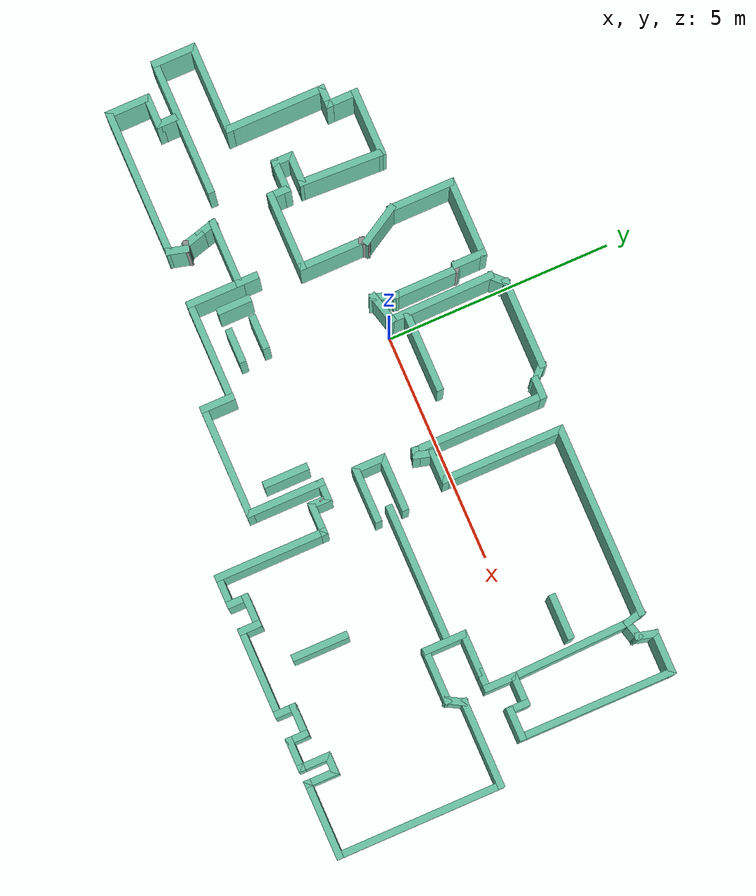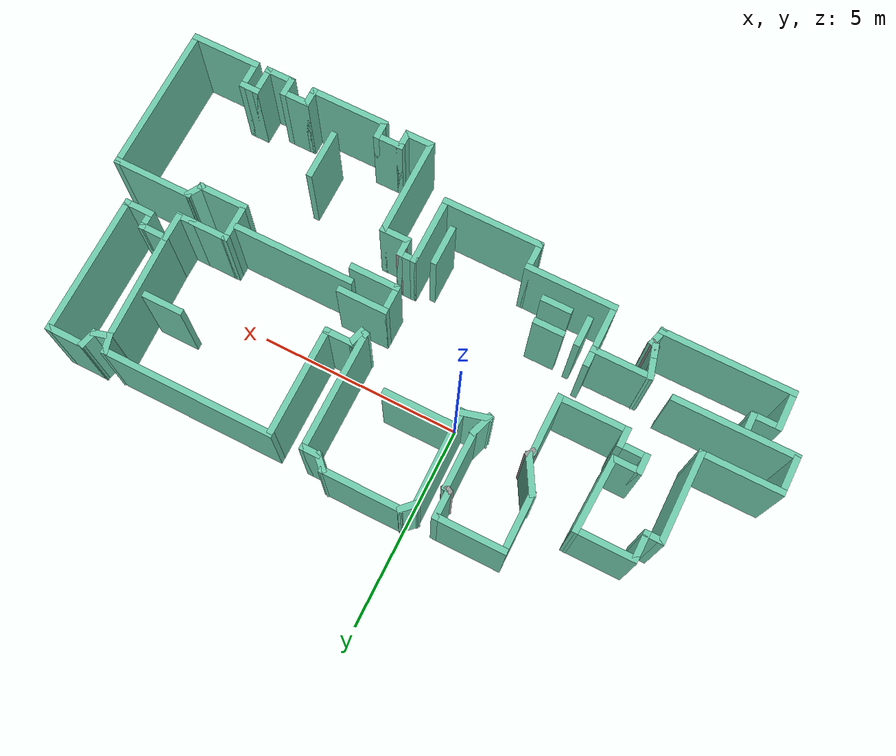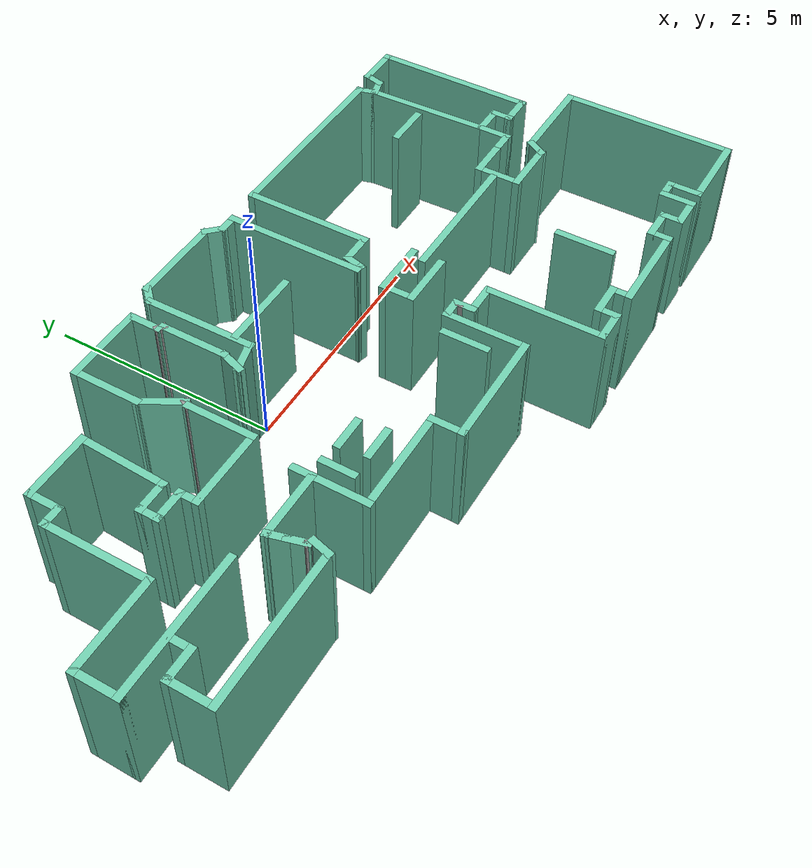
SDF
<?xml version='1.0'?>
<sdf version='1.6'>
  <model name='map_8'>
    <pose frame=''>1.27154 -1.32624 0 0 -0 0</pose>
    <link name='Wall_0'>
      <collision name='Wall_0_Collision'>
        <geometry>
          <box>
            <size>1.5 0.15 2.5</size>
          </box>
        </geometry>
        <pose frame=''>0 0 1.25 0 -0 0</pose>
      </collision>
      <visual name='Wall_0_Visual'>
        <pose frame=''>0 0 1.25 0 -0 0</pose>
        <geometry>
          <box>
            <size>1.5 0.15 2.5</size>
          </box>
        </geometry>
        <material>
          <script>
            <uri>file://media/materials/scripts/gazebo.material</uri>
            <name>Gazebo/Grey</name>
          </script>
          <ambient>0.435294 0.796078 0.67451 1</ambient>
        </material>
        <meta>
          <layer>0</layer>
        </meta>
      </visual>
      <pose frame=''>-5.35674 2.63095 0 0 -0 3.14159</pose>
    </link>
    <link name='Wall_1'>
      <collision name='Wall_1_Collision'>
        <geometry>
          <box>
            <size>0.75 0.15 2.5</size>
          </box>
        </geometry>
        <pose frame=''>0 0 1.25 0 -0 0</pose>
      </collision>
      <visual name='Wall_1_Visual'>
        <pose frame=''>0 0 1.25 0 -0 0</pose>
        <geometry>
          <box>
            <size>0.75 0.15 2.5</size>
          </box>
        </geometry>
        <material>
          <script>
            <uri>file://media/materials/scripts/gazebo.material</uri>
            <name>Gazebo/Grey</name>
          </script>
          <ambient>0.435294 0.796078 0.67451 1</ambient>
        </material>
        <meta>
          <layer>0</layer>
        </meta>
      </visual>
      <pose frame=''>-6.03174 2.33095 0 0 -0 -1.5708</pose>
    </link>
    <link name='Wall_100'>
      <collision name='Wall_100_Collision'>
        <geometry>
          <box>
            <size>0.5 0.15 2.5</size>
          </box>
        </geometry>
        <pose frame=''>0 0 1.25 0 -0 0</pose>
      </collision>
      <visual name='Wall_100_Visual'>
        <pose frame=''>0 0 1.25 0 -0 0</pose>
        <geometry>
          <box>
            <size>0.5 0.15 2.5</size>
          </box>
        </geometry>
        <material>
          <script>
            <uri>file://media/materials/scripts/gazebo.material</uri>
            <name>Gazebo/Grey</name>
          </script>
          <ambient>0.435294 0.796078 0.67451 1</ambient>
        </material>
        <meta>
          <layer>0</layer>
        </meta>
      </visual>
      <pose frame=''>-4.76082 0.357873 0 0 -0 1.5708</pose>
    </link>
    <link name='Wall_101'>
      <collision name='Wall_101_Collision'>
        <geometry>
          <box>
            <size>0.75 0.15 2.5</size>
          </box>
        </geometry>
        <pose frame=''>0 0 1.25 0 -0 0</pose>
      </collision>
      <visual name='Wall_101_Visual'>
        <pose frame=''>0 0 1.25 0 -0 0</pose>
        <geometry>
          <box>
            <size>0.75 0.15 2.5</size>
          </box>
        </geometry>
        <material>
          <script>
            <uri>file://media/materials/scripts/gazebo.material</uri>
            <name>Gazebo/Grey</name>
          </script>
          <ambient>0.435294 0.796078 0.67451 1</ambient>
        </material>
        <meta>
          <layer>0</layer>
        </meta>
      </visual>
      <pose frame=''>-5.06081 0.532873 0 0 -0 3.14159</pose>
    </link>
    <link name='Wall_102'>
      <collision name='Wall_102_Collision'>
        <geometry>
          <box>
            <size>0.5 0.15 2.5</size>
          </box>
        </geometry>
        <pose frame=''>0 0 1.25 0 -0 0</pose>
      </collision>
      <visual name='Wall_102_Visual'>
        <pose frame=''>0 0 1.25 0 -0 0</pose>
        <geometry>
          <box>
            <size>0.5 0.15 2.5</size>
          </box>
        </geometry>
        <material>
          <script>
            <uri>file://media/materials/scripts/gazebo.material</uri>
            <name>Gazebo/Grey</name>
          </script>
          <ambient>0.435294 0.796078 0.67451 1</ambient>
        </material>
        <meta>
          <layer>0</layer>
        </meta>
      </visual>
      <pose frame=''>-5.36081 0.707873 0 0 -0 1.5708</pose>
    </link>
    <link name='Wall_103'>
      <collision name='Wall_103_Collision'>
        <geometry>
          <box>
            <size>0.75 0.15 2.5</size>
          </box>
        </geometry>
        <pose frame=''>0 0 1.25 0 -0 0</pose>
      </collision>
      <visual name='Wall_103_Visual'>
        <pose frame=''>0 0 1.25 0 -0 0</pose>
        <geometry>
          <box>
            <size>0.75 0.15 2.5</size>
          </box>
        </geometry>
        <material>
          <script>
            <uri>file://media/materials/scripts/gazebo.material</uri>
            <name>Gazebo/Grey</name>
          </script>
          <ambient>0.435294 0.796078 0.67451 1</ambient>
        </material>
        <meta>
          <layer>0</layer>
        </meta>
      </visual>
      <pose frame=''>-5.06081 0.882873 0 0 -0 0</pose>
    </link>
    <link name='Wall_104'>
      <collision name='Wall_104_Collision'>
        <geometry>
          <box>
            <size>1.89986 0.15 2.5</size>
          </box>
        </geometry>
        <pose frame=''>0 0 1.25 0 -0 0</pose>
      </collision>
      <visual name='Wall_104_Visual'>
        <pose frame=''>0 0 1.25 0 -0 0</pose>
        <geometry>
          <box>
            <size>1.89986 0.15 2.5</size>
          </box>
        </geometry>
        <material>
          <script>
            <uri>file://media/materials/scripts/gazebo.material</uri>
            <name>Gazebo/Grey</name>
          </script>
          <ambient>0.435294 0.796078 0.67451 1</ambient>
        </material>
        <meta>
          <layer>0</layer>
        </meta>
      </visual>
      <pose frame=''>-4.72128 1.75691 0 0 -0 1.52559</pose>
    </link>
    <link name='Wall_106'>
      <collision name='Wall_106_Collision'>
        <geometry>
          <box>
            <size>1 0.15 2.5</size>
          </box>
        </geometry>
        <pose frame=''>0 0 1.25 0 -0 0</pose>
      </collision>
      <visual name='Wall_106_Visual'>
        <pose frame=''>0 0 1.25 0 -0 0</pose>
        <geometry>
          <box>
            <size>1 0.15 2.5</size>
          </box>
        </geometry>
        <material>
          <script>
            <uri>file://media/materials/scripts/gazebo.material</uri>
            <name>Gazebo/Grey</name>
          </script>
          <ambient>0.435294 0.796078 0.67451 1</ambient>
        </material>
        <meta>
          <layer>0</layer>
        </meta>
      </visual>
      <pose frame=''>5.57376 2.19147 0 0 -0 0</pose>
    </link>
    <link name='Wall_108'>
      <collision name='Wall_108_Collision'>
        <geometry>
          <box>
            <size>2.72254 0.15 2.5</size>
          </box>
        </geometry>
        <pose frame=''>0 0 1.25 0 -0 0</pose>
      </collision>
      <visual name='Wall_108_Visual'>
        <pose frame=''>0 0 1.25 0 -0 0</pose>
        <geometry>
          <box>
            <size>2.72254 0.15 2.5</size>
          </box>
        </geometry>
        <material>
          <script>
            <uri>file://media/materials/scripts/gazebo.material</uri>
            <name>Gazebo/Grey</name>
          </script>
          <ambient>0.435294 0.796078 0.67451 1</ambient>
        </material>
        <meta>
          <layer>0</layer>
        </meta>
      </visual>
      <pose frame=''>6.26741 2.09623 0 0 -0 -1.54021</pose>
    </link>
    <link name='Wall_11'>
      <collision name='Wall_11_Collision'>
        <geometry>
          <box>
            <size>0.75 0.15 2.5</size>
          </box>
        </geometry>
        <pose frame=''>0 0 1.25 0 -0 0</pose>
      </collision>
      <visual name='Wall_11_Visual'>
        <pose frame=''>0 0 1.25 0 -0 0</pose>
        <geometry>
          <box>
            <size>0.75 0.15 2.5</size>
          </box>
        </geometry>
        <material>
          <script>
            <uri>file://media/materials/scripts/gazebo.material</uri>
            <name>Gazebo/Grey</name>
          </script>
          <ambient>0.435294 0.796078 0.67451 1</ambient>
        </material>
        <meta>
          <layer>0</layer>
        </meta>
      </visual>
      <pose frame=''>-7.34107 -1.35055 0 0 -0 3.14159</pose>
    </link>
    <link name='Wall_113'>
      <collision name='Wall_113_Collision'>
        <geometry>
          <box>
            <size>1.75 0.15 2.5</size>
          </box>
        </geometry>
        <pose frame=''>0 0 1.25 0 -0 0</pose>
      </collision>
      <visual name='Wall_113_Visual'>
        <pose frame=''>0 0 1.25 0 -0 0</pose>
        <geometry>
          <box>
            <size>1.75 0.15 2.5</size>
          </box>
        </geometry>
        <material>
          <script>
            <uri>file://media/materials/scripts/gazebo.material</uri>
            <name>Gazebo/Grey</name>
          </script>
          <ambient>0.435294 0.796078 0.67451 1</ambient>
        </material>
        <meta>
          <layer>0</layer>
        </meta>
      </visual>
      <pose frame=''>-0.554925 1.77512 0 0 -0 3.14159</pose>
    </link>
    <link name='Wall_115'>
      <collision name='Wall_115_Collision'>
        <geometry>
          <box>
            <size>3 0.15 2.5</size>
          </box>
        </geometry>
        <pose frame=''>0 0 1.25 0 -0 0</pose>
      </collision>
      <visual name='Wall_115_Visual'>
        <pose frame=''>0 0 1.25 0 -0 0</pose>
        <geometry>
          <box>
            <size>3 0.15 2.5</size>
          </box>
        </geometry>
        <material>
          <script>
            <uri>file://media/materials/scripts/gazebo.material</uri>
            <name>Gazebo/Grey</name>
          </script>
          <ambient>0.435294 0.796078 0.67451 1</ambient>
        </material>
        <meta>
          <layer>0</layer>
        </meta>
      </visual>
      <pose frame=''>3.56185 -0.144722 0 0 -0 3.14159</pose>
    </link>
    <link name='Wall_118'>
      <collision name='Wall_118_Collision'>
        <geometry>
          <box>
            <size>0.75 0.15 2.5</size>
          </box>
        </geometry>
        <pose frame=''>0 0 1.25 0 -0 0</pose>
      </collision>
      <visual name='Wall_118_Visual'>
        <pose frame=''>0 0 1.25 0 -0 0</pose>
        <geometry>
          <box>
            <size>0.75 0.15 2.5</size>
          </box>
        </geometry>
        <material>
          <script>
            <uri>file://media/materials/scripts/gazebo.material</uri>
            <name>Gazebo/Grey</name>
          </script>
          <ambient>0.435294 0.796078 0.67451 1</ambient>
        </material>
        <meta>
          <layer>0</layer>
        </meta>
      </visual>
      <pose frame=''>1.12404 -0.167155 0 0 -0 -1.5708</pose>
    </link>
    <link name='Wall_119'>
      <collision name='Wall_119_Collision'>
        <geometry>
          <box>
            <size>1.25 0.15 2.5</size>
          </box>
        </geometry>
        <pose frame=''>0 0 1.25 0 -0 0</pose>
      </collision>
      <visual name='Wall_119_Visual'>
        <pose frame=''>0 0 1.25 0 -0 0</pose>
        <geometry>
          <box>
            <size>1.25 0.15 2.5</size>
          </box>
        </geometry>
        <material>
          <script>
            <uri>file://media/materials/scripts/gazebo.material</uri>
            <name>Gazebo/Grey</name>
          </script>
          <ambient>0.435294 0.796078 0.67451 1</ambient>
        </material>
        <meta>
          <layer>0</layer>
        </meta>
      </visual>
      <pose frame=''>1.67404 -0.467155 0 0 -0 0</pose>
    </link>
    <link name='Wall_12'>
      <collision name='Wall_12_Collision'>
        <geometry>
          <box>
            <size>1 0.15 2.5</size>
          </box>
        </geometry>
        <pose frame=''>0 0 1.25 0 -0 0</pose>
      </collision>
      <visual name='Wall_12_Visual'>
        <pose frame=''>0 0 1.25 0 -0 0</pose>
        <geometry>
          <box>
            <size>1 0.15 2.5</size>
          </box>
        </geometry>
        <material>
          <script>
            <uri>file://media/materials/scripts/gazebo.material</uri>
            <name>Gazebo/Grey</name>
          </script>
          <ambient>0.435294 0.796078 0.67451 1</ambient>
        </material>
        <meta>
          <layer>0</layer>
        </meta>
      </visual>
      <pose frame=''>-7.64107 -1.77555 0 0 -0 -1.5708</pose>
    </link>
    <link name='Wall_121'>
      <collision name='Wall_121_Collision'>
        <geometry>
          <box>
            <size>1.25 0.15 2.5</size>
          </box>
        </geometry>
        <pose frame=''>0 0 1.25 0 -0 0</pose>
      </collision>
      <visual name='Wall_121_Visual'>
        <pose frame=''>0 0 1.25 0 -0 0</pose>
        <geometry>
          <box>
            <size>1.25 0.15 2.5</size>
          </box>
        </geometry>
        <material>
          <script>
            <uri>file://media/materials/scripts/gazebo.material</uri>
            <name>Gazebo/Grey</name>
          </script>
          <ambient>0.435294 0.796078 0.67451 1</ambient>
        </material>
        <meta>
          <layer>0</layer>
        </meta>
      </visual>
      <pose frame=''>1.67404 0.132845 0 0 -0 0</pose>
    </link>
    <link name='Wall_123'>
      <collision name='Wall_123_Collision'>
        <geometry>
          <box>
            <size>1.25 0.15 2.5</size>
          </box>
        </geometry>
        <pose frame=''>0 0 1.25 0 -0 0</pose>
      </collision>
      <visual name='Wall_123_Visual'>
        <pose frame=''>0 0 1.25 0 -0 0</pose>
        <geometry>
          <box>
            <size>1.25 0.15 2.5</size>
          </box>
        </geometry>
        <material>
          <script>
            <uri>file://media/materials/scripts/gazebo.material</uri>
            <name>Gazebo/Grey</name>
          </script>
          <ambient>0.435294 0.796078 0.67451 1</ambient>
        </material>
        <meta>
          <layer>0</layer>
        </meta>
      </visual>
      <pose frame=''>4.15415 -2.59143 0 0 -0 -1.5708</pose>
    </link>
    <link name='Wall_125'>
      <collision name='Wall_125_Collision'>
        <geometry>
          <box>
            <size>0.75 0.15 2.5</size>
          </box>
        </geometry>
        <pose frame=''>0 0 1.25 0 -0 0</pose>
      </collision>
      <visual name='Wall_125_Visual'>
        <pose frame=''>0 0 1.25 0 -0 0</pose>
        <geometry>
          <box>
            <size>0.75 0.15 2.5</size>
          </box>
        </geometry>
        <material>
          <script>
            <uri>file://media/materials/scripts/gazebo.material</uri>
            <name>Gazebo/Grey</name>
          </script>
          <ambient>0.435294 0.796078 0.67451 1</ambient>
        </material>
        <meta>
          <layer>0</layer>
        </meta>
      </visual>
      <pose frame=''>-2.99321 -1.41621 0 0 -0 -1.5708</pose>
    </link>
    <link name='Wall_128'>
      <collision name='Wall_128_Collision'>
        <geometry>
          <box>
            <size>0.75 0.15 2.5</size>
          </box>
        </geometry>
        <pose frame=''>0 0 1.25 0 -0 0</pose>
      </collision>
      <visual name='Wall_128_Visual'>
        <pose frame=''>0 0 1.25 0 -0 0</pose>
        <geometry>
          <box>
            <size>0.75 0.15 2.5</size>
          </box>
        </geometry>
        <material>
          <script>
            <uri>file://media/materials/scripts/gazebo.material</uri>
            <name>Gazebo/Grey</name>
          </script>
          <ambient>0.435294 0.796078 0.67451 1</ambient>
        </material>
        <meta>
          <layer>0</layer>
        </meta>
      </visual>
      <pose frame=''>-2.27686 -1.16247 0 0 -0 0</pose>
    </link>
    <link name='Wall_13'>
      <collision name='Wall_13_Collision'>
        <geometry>
          <box>
            <size>3.25 0.15 2.5</size>
          </box>
        </geometry>
        <pose frame=''>0 0 1.25 0 -0 0</pose>
      </collision>
      <visual name='Wall_13_Visual'>
        <pose frame=''>0 0 1.25 0 -0 0</pose>
        <geometry>
          <box>
            <size>3.25 0.15 2.5</size>
          </box>
        </geometry>
        <material>
          <script>
            <uri>file://media/materials/scripts/gazebo.material</uri>
            <name>Gazebo/Grey</name>
          </script>
          <ambient>0.435294 0.796078 0.67451 1</ambient>
        </material>
        <meta>
          <layer>0</layer>
        </meta>
      </visual>
      <pose frame=''>-6.09107 -2.20056 0 0 -0 0</pose>
    </link>
    <link name='Wall_130'>
      <collision name='Wall_130_Collision'>
        <geometry>
          <box>
            <size>0.75 0.15 2.5</size>
          </box>
        </geometry>
        <pose frame=''>0 0 1.25 0 -0 0</pose>
      </collision>
      <visual name='Wall_130_Visual'>
        <pose frame=''>0 0 1.25 0 -0 0</pose>
        <geometry>
          <box>
            <size>0.75 0.15 2.5</size>
          </box>
        </geometry>
        <material>
          <script>
            <uri>file://media/materials/scripts/gazebo.material</uri>
            <name>Gazebo/Grey</name>
          </script>
          <ambient>0.435294 0.796078 0.67451 1</ambient>
        </material>
        <meta>
          <layer>0</layer>
        </meta>
      </visual>
      <pose frame=''>-2.20747 -1.7176 0 0 -0 0</pose>
    </link>
    <link name='Wall_132'>
      <collision name='Wall_132_Collision'>
        <geometry>
          <box>
            <size>1 0.15 2.5</size>
          </box>
        </geometry>
        <pose frame=''>0 0 1.25 0 -0 0</pose>
      </collision>
      <visual name='Wall_132_Visual'>
        <pose frame=''>0 0 1.25 0 -0 0</pose>
        <geometry>
          <box>
            <size>1 0.15 2.5</size>
          </box>
        </geometry>
        <material>
          <script>
            <uri>file://media/materials/scripts/gazebo.material</uri>
            <name>Gazebo/Grey</name>
          </script>
          <ambient>0.435294 0.796078 0.67451 1</ambient>
        </material>
        <meta>
          <layer>0</layer>
        </meta>
      </visual>
      <pose frame=''>0.661426 -1.84191 0 0 -0 -1.5708</pose>
    </link>
    <link name='Wall_14'>
      <collision name='Wall_14_Collision'>
        <geometry>
          <box>
            <size>0.5 0.15 2.5</size>
          </box>
        </geometry>
        <pose frame=''>0 0 1.25 0 -0 0</pose>
      </collision>
      <visual name='Wall_14_Visual'>
        <pose frame=''>0 0 1.25 0 -0 0</pose>
        <geometry>
          <box>
            <size>0.5 0.15 2.5</size>
          </box>
        </geometry>
        <material>
          <script>
            <uri>file://media/materials/scripts/gazebo.material</uri>
            <name>Gazebo/Grey</name>
          </script>
          <ambient>0.435294 0.796078 0.67451 1</ambient>
        </material>
        <meta>
          <layer>0</layer>
        </meta>
      </visual>
      <pose frame=''>-4.49577 -2.03152 0 0 -0 1.309</pose>
    </link>
    <link name='Wall_15'>
      <collision name='Wall_15_Collision'>
        <geometry>
          <box>
            <size>0.25 0.15 2.5</size>
          </box>
        </geometry>
        <pose frame=''>0 0 1.25 0 -0 0</pose>
      </collision>
      <visual name='Wall_15_Visual'>
        <pose frame=''>0 0 1.25 0 -0 0</pose>
        <geometry>
          <box>
            <size>0.25 0.15 2.5</size>
          </box>
        </geometry>
        <material>
          <script>
            <uri>file://media/materials/scripts/gazebo.material</uri>
            <name>Gazebo/Grey</name>
          </script>
          <ambient>1 1 1 1</ambient>
        </material>
        <meta>
          <layer>0</layer>
        </meta>
      </visual>
      <pose frame=''>-4.49378 -1.83748 0 0 -0 2.61799</pose>
    </link>
    <link name='Wall_16'>
      <collision name='Wall_16_Collision'>
        <geometry>
          <box>
            <size>0.5 0.15 2.5</size>
          </box>
        </geometry>
        <pose frame=''>0 0 1.25 0 -0 0</pose>
      </collision>
      <visual name='Wall_16_Visual'>
        <pose frame=''>0 0 1.25 0 -0 0</pose>
        <geometry>
          <box>
            <size>0.5 0.15 2.5</size>
          </box>
        </geometry>
        <material>
          <script>
            <uri>file://media/materials/scripts/gazebo.material</uri>
            <name>Gazebo/Grey</name>
          </script>
          <ambient>0.435294 0.796078 0.67451 1</ambient>
        </material>
        <meta>
          <layer>0</layer>
        </meta>
      </visual>
      <pose frame=''>-4.58237 -1.64344 0 0 -0 1.8326</pose>
    </link>
    <link name='Wall_17'>
      <collision name='Wall_17_Collision'>
        <geometry>
          <box>
            <size>0.5 0.15 2.5</size>
          </box>
        </geometry>
        <pose frame=''>0 0 1.25 0 -0 0</pose>
      </collision>
      <visual name='Wall_17_Visual'>
        <pose frame=''>0 0 1.25 0 -0 0</pose>
        <geometry>
          <box>
            <size>0.5 0.15 2.5</size>
          </box>
        </geometry>
        <material>
          <script>
            <uri>file://media/materials/scripts/gazebo.material</uri>
            <name>Gazebo/Grey</name>
          </script>
          <ambient>0.435294 0.796078 0.67451 1</ambient>
        </material>
        <meta>
          <layer>0</layer>
        </meta>
      </visual>
      <pose frame=''>-4.67296 -1.30537 0 0 -0 1.8326</pose>
    </link>
    <link name='Wall_2'>
      <collision name='Wall_2_Collision'>
        <geometry>
          <box>
            <size>0.5 0.15 2.5</size>
          </box>
        </geometry>
        <pose frame=''>0 0 1.25 0 -0 0</pose>
      </collision>
      <visual name='Wall_2_Visual'>
        <pose frame=''>0 0 1.25 0 -0 0</pose>
        <geometry>
          <box>
            <size>0.5 0.15 2.5</size>
          </box>
        </geometry>
        <material>
          <script>
            <uri>file://media/materials/scripts/gazebo.material</uri>
            <name>Gazebo/Grey</name>
          </script>
          <ambient>0.435294 0.796078 0.67451 1</ambient>
        </material>
        <meta>
          <layer>0</layer>
        </meta>
      </visual>
      <pose frame=''>-6.20674 2.03095 0 0 -0 3.14159</pose>
    </link>
    <link name='Wall_20'>
      <collision name='Wall_20_Collision'>
        <geometry>
          <box>
            <size>1.5 0.15 2.5</size>
          </box>
        </geometry>
        <pose frame=''>0 0 1.25 0 -0 0</pose>
      </collision>
      <visual name='Wall_20_Visual'>
        <pose frame=''>0 0 1.25 0 -0 0</pose>
        <geometry>
          <box>
            <size>1.5 0.15 2.5</size>
          </box>
        </geometry>
        <material>
          <script>
            <uri>file://media/materials/scripts/gazebo.material</uri>
            <name>Gazebo/Grey</name>
          </script>
          <ambient>0.435294 0.796078 0.67451 1</ambient>
        </material>
        <meta>
          <layer>0</layer>
        </meta>
      </visual>
      <pose frame=''>-4.04326 -1.13633 0 0 -0 0</pose>
    </link>
    <link name='Wall_21'>
      <collision name='Wall_21_Collision'>
        <geometry>
          <box>
            <size>0.5 0.15 2.5</size>
          </box>
        </geometry>
        <pose frame=''>0 0 1.25 0 -0 0</pose>
      </collision>
      <visual name='Wall_21_Visual'>
        <pose frame=''>0 0 1.25 0 -0 0</pose>
        <geometry>
          <box>
            <size>0.5 0.15 2.5</size>
          </box>
        </geometry>
        <material>
          <script>
            <uri>file://media/materials/scripts/gazebo.material</uri>
            <name>Gazebo/Grey</name>
          </script>
          <ambient>0.435294 0.796078 0.67451 1</ambient>
        </material>
        <meta>
          <layer>0</layer>
        </meta>
      </visual>
      <pose frame=''>-3.36825 -0.961333 0 0 -0 1.5708</pose>
    </link>
    <link name='Wall_25'>
      <collision name='Wall_25_Collision'>
        <geometry>
          <box>
            <size>1.25 0.15 2.5</size>
          </box>
        </geometry>
        <pose frame=''>0 0 1.25 0 -0 0</pose>
      </collision>
      <visual name='Wall_25_Visual'>
        <pose frame=''>0 0 1.25 0 -0 0</pose>
        <geometry>
          <box>
            <size>1.25 0.15 2.5</size>
          </box>
        </geometry>
        <material>
          <script>
            <uri>file://media/materials/scripts/gazebo.material</uri>
            <name>Gazebo/Grey</name>
          </script>
          <ambient>0.435294 0.796078 0.67451 1</ambient>
        </material>
        <meta>
          <layer>0</layer>
        </meta>
      </visual>
      <pose frame=''>-3.36825 -1.68633 0 0 -0 -1.5708</pose>
    </link>
    <link name='Wall_26'>
      <collision name='Wall_26_Collision'>
        <geometry>
          <box>
            <size>2.25 0.15 2.5</size>
          </box>
        </geometry>
        <pose frame=''>0 0 1.25 0 -0 0</pose>
      </collision>
      <visual name='Wall_26_Visual'>
        <pose frame=''>0 0 1.25 0 -0 0</pose>
        <geometry>
          <box>
            <size>2.25 0.15 2.5</size>
          </box>
        </geometry>
        <material>
          <script>
            <uri>file://media/materials/scripts/gazebo.material</uri>
            <name>Gazebo/Grey</name>
          </script>
          <ambient>0.435294 0.796078 0.67451 1</ambient>
        </material>
        <meta>
          <layer>0</layer>
        </meta>
      </visual>
      <pose frame=''>-2.31826 -2.23633 0 0 -0 0</pose>
    </link>
    <link name='Wall_27'>
      <collision name='Wall_27_Collision'>
        <geometry>
          <box>
            <size>0.75 0.15 2.5</size>
          </box>
        </geometry>
        <pose frame=''>0 0 1.25 0 -0 0</pose>
      </collision>
      <visual name='Wall_27_Visual'>
        <pose frame=''>0 0 1.25 0 -0 0</pose>
        <geometry>
          <box>
            <size>0.75 0.15 2.5</size>
          </box>
        </geometry>
        <material>
          <script>
            <uri>file://media/materials/scripts/gazebo.material</uri>
            <name>Gazebo/Grey</name>
          </script>
          <ambient>0.435294 0.796078 0.67451 1</ambient>
        </material>
        <meta>
          <layer>0</layer>
        </meta>
      </visual>
      <pose frame=''>-1.26825 -2.53633 0 0 -0 -1.5708</pose>
    </link>
    <link name='Wall_3'>
      <collision name='Wall_3_Collision'>
        <geometry>
          <box>
            <size>2.25 0.15 2.5</size>
          </box>
        </geometry>
        <pose frame=''>0 0 1.25 0 -0 0</pose>
      </collision>
      <visual name='Wall_3_Visual'>
        <pose frame=''>0 0 1.25 0 -0 0</pose>
        <geometry>
          <box>
            <size>2.25 0.15 2.5</size>
          </box>
        </geometry>
        <material>
          <script>
            <uri>file://media/materials/scripts/gazebo.material</uri>
            <name>Gazebo/Grey</name>
          </script>
          <ambient>0.435294 0.796078 0.67451 1</ambient>
        </material>
        <meta>
          <layer>0</layer>
        </meta>
      </visual>
      <pose frame=''>-6.38174 0.980951 0 0 -0 -1.5708</pose>
    </link>
    <link name='Wall_30'>
      <collision name='Wall_30_Collision'>
        <geometry>
          <box>
            <size>2.5 0.15 2.5</size>
          </box>
        </geometry>
        <pose frame=''>0 0 1.25 0 -0 0</pose>
      </collision>
      <visual name='Wall_30_Visual'>
        <pose frame=''>0 0 1.25 0 -0 0</pose>
        <geometry>
          <box>
            <size>2.5 0.15 2.5</size>
          </box>
        </geometry>
        <material>
          <script>
            <uri>file://media/materials/scripts/gazebo.material</uri>
            <name>Gazebo/Grey</name>
          </script>
          <ambient>0.435294 0.796078 0.67451 1</ambient>
        </material>
        <meta>
          <layer>0</layer>
        </meta>
      </visual>
      <pose frame=''>-0.093255 -2.83633 0 0 -0 0</pose>
    </link>
    <link name='Wall_31'>
      <collision name='Wall_31_Collision'>
        <geometry>
          <box>
            <size>1.75 0.15 2.5</size>
          </box>
        </geometry>
        <pose frame=''>0 0 1.25 0 -0 0</pose>
      </collision>
      <visual name='Wall_31_Visual'>
        <pose frame=''>0 0 1.25 0 -0 0</pose>
        <geometry>
          <box>
            <size>1.75 0.15 2.5</size>
          </box>
        </geometry>
        <material>
          <script>
            <uri>file://media/materials/scripts/gazebo.material</uri>
            <name>Gazebo/Grey</name>
          </script>
          <ambient>0.435294 0.796078 0.67451 1</ambient>
        </material>
        <meta>
          <layer>0</layer>
        </meta>
      </visual>
      <pose frame=''>1.08174 -2.03633 0 0 -0 1.5708</pose>
    </link>
    <link name='Wall_32'>
      <collision name='Wall_32_Collision'>
        <geometry>
          <box>
            <size>0.5 0.15 2.5</size>
          </box>
        </geometry>
        <pose frame=''>0 0 1.25 0 -0 0</pose>
      </collision>
      <visual name='Wall_32_Visual'>
        <pose frame=''>0 0 1.25 0 -0 0</pose>
        <geometry>
          <box>
            <size>0.5 0.15 2.5</size>
          </box>
        </geometry>
        <material>
          <script>
            <uri>file://media/materials/scripts/gazebo.material</uri>
            <name>Gazebo/Grey</name>
          </script>
          <ambient>0.435294 0.796078 0.67451 1</ambient>
        </material>
        <meta>
          <layer>0</layer>
        </meta>
      </visual>
      <pose frame=''>1.25675 -1.23633 0 0 -0 0</pose>
    </link>
    <link name='Wall_33'>
      <collision name='Wall_33_Collision'>
        <geometry>
          <box>
            <size>0.25 0.15 2.5</size>
          </box>
        </geometry>
        <pose frame=''>0 0 1.25 0 -0 0</pose>
      </collision>
      <visual name='Wall_33_Visual'>
        <pose frame=''>0 0 1.25 0 -0 0</pose>
        <geometry>
          <box>
            <size>0.25 0.15 2.5</size>
          </box>
        </geometry>
        <material>
          <script>
            <uri>file://media/materials/scripts/gazebo.material</uri>
            <name>Gazebo/Grey</name>
          </script>
          <ambient>1 1 1 1</ambient>
        </material>
        <meta>
          <layer>0</layer>
        </meta>
      </visual>
      <pose frame=''>1.43175 -1.28633 0 0 -0 -1.5708</pose>
    </link>
    <link name='Wall_36'>
      <collision name='Wall_36_Collision'>
        <geometry>
          <box>
            <size>0.5 0.15 2.5</size>
          </box>
        </geometry>
        <pose frame=''>0 0 1.25 0 -0 0</pose>
      </collision>
      <visual name='Wall_36_Visual'>
        <pose frame=''>0 0 1.25 0 -0 0</pose>
        <geometry>
          <box>
            <size>0.5 0.15 2.5</size>
          </box>
        </geometry>
        <material>
          <script>
            <uri>file://media/materials/scripts/gazebo.material</uri>
            <name>Gazebo/Grey</name>
          </script>
          <ambient>0.435294 0.796078 0.67451 1</ambient>
        </material>
        <meta>
          <layer>0</layer>
        </meta>
      </visual>
      <pose frame=''>1.43175 -1.41133 0 0 -0 -1.5708</pose>
    </link>
    <link name='Wall_39'>
      <collision name='Wall_39_Collision'>
        <geometry>
          <box>
            <size>0.75 0.15 2.5</size>
          </box>
        </geometry>
        <pose frame=''>0 0 1.25 0 -0 0</pose>
      </collision>
      <visual name='Wall_39_Visual'>
        <pose frame=''>0 0 1.25 0 -0 0</pose>
        <geometry>
          <box>
            <size>0.75 0.15 2.5</size>
          </box>
        </geometry>
        <material>
          <script>
            <uri>file://media/materials/scripts/gazebo.material</uri>
            <name>Gazebo/Grey</name>
          </script>
          <ambient>0.435294 0.796078 0.67451 1</ambient>
        </material>
        <meta>
          <layer>0</layer>
        </meta>
      </visual>
      <pose frame=''>1.73175 -1.58633 0 0 -0 0</pose>
    </link>
    <link name='Wall_4'>
      <collision name='Wall_4_Collision'>
        <geometry>
          <box>
            <size>2 0.15 2.5</size>
          </box>
        </geometry>
        <pose frame=''>0 0 1.25 0 -0 0</pose>
      </collision>
      <visual name='Wall_4_Visual'>
        <pose frame=''>0 0 1.25 0 -0 0</pose>
        <geometry>
          <box>
            <size>2 0.15 2.5</size>
          </box>
        </geometry>
        <material>
          <script>
            <uri>file://media/materials/scripts/gazebo.material</uri>
            <name>Gazebo/Grey</name>
          </script>
          <ambient>0.435294 0.796078 0.67451 1</ambient>
        </material>
        <meta>
          <layer>0</layer>
        </meta>
      </visual>
      <pose frame=''>-7.30674 -0.069049 0 0 -0 3.14159</pose>
    </link>
    <link name='Wall_40'>
      <collision name='Wall_40_Collision'>
        <geometry>
          <box>
            <size>2.5 0.15 2.5</size>
          </box>
        </geometry>
        <pose frame=''>0 0 1.25 0 -0 0</pose>
      </collision>
      <visual name='Wall_40_Visual'>
        <pose frame=''>0 0 1.25 0 -0 0</pose>
        <geometry>
          <box>
            <size>2.5 0.15 2.5</size>
          </box>
        </geometry>
        <material>
          <script>
            <uri>file://media/materials/scripts/gazebo.material</uri>
            <name>Gazebo/Grey</name>
          </script>
          <ambient>0.435294 0.796078 0.67451 1</ambient>
        </material>
        <meta>
          <layer>0</layer>
        </meta>
      </visual>
      <pose frame=''>2.03174 -2.76133 0 0 -0 -1.5708</pose>
    </link>
    <link name='Wall_41'>
      <collision name='Wall_41_Collision'>
        <geometry>
          <box>
            <size>0.75 0.15 2.5</size>
          </box>
        </geometry>
        <pose frame=''>0 0 1.25 0 -0 0</pose>
      </collision>
      <visual name='Wall_41_Visual'>
        <pose frame=''>0 0 1.25 0 -0 0</pose>
        <geometry>
          <box>
            <size>0.75 0.15 2.5</size>
          </box>
        </geometry>
        <material>
          <script>
            <uri>file://media/materials/scripts/gazebo.material</uri>
            <name>Gazebo/Grey</name>
          </script>
          <ambient>0.435294 0.796078 0.67451 1</ambient>
        </material>
        <meta>
          <layer>0</layer>
        </meta>
      </visual>
      <pose frame=''>2.33175 -3.93633 0 0 -0 0</pose>
    </link>
    <link name='Wall_42'>
      <collision name='Wall_42_Collision'>
        <geometry>
          <box>
            <size>0.5 0.15 2.5</size>
          </box>
        </geometry>
        <pose frame=''>0 0 1.25 0 -0 0</pose>
      </collision>
      <visual name='Wall_42_Visual'>
        <pose frame=''>0 0 1.25 0 -0 0</pose>
        <geometry>
          <box>
            <size>0.5 0.15 2.5</size>
          </box>
        </geometry>
        <material>
          <script>
            <uri>file://media/materials/scripts/gazebo.material</uri>
            <name>Gazebo/Grey</name>
          </script>
          <ambient>0.435294 0.796078 0.67451 1</ambient>
        </material>
        <meta>
          <layer>0</layer>
        </meta>
      </visual>
      <pose frame=''>2.63175 -3.76133 0 0 -0 1.5708</pose>
    </link>
    <link name='Wall_43'>
      <collision name='Wall_43_Collision'>
        <geometry>
          <box>
            <size>0.75 0.15 2.5</size>
          </box>
        </geometry>
        <pose frame=''>0 0 1.25 0 -0 0</pose>
      </collision>
      <visual name='Wall_43_Visual'>
        <pose frame=''>0 0 1.25 0 -0 0</pose>
        <geometry>
          <box>
            <size>0.75 0.15 2.5</size>
          </box>
        </geometry>
        <material>
          <script>
            <uri>file://media/materials/scripts/gazebo.material</uri>
            <name>Gazebo/Grey</name>
          </script>
          <ambient>0.435294 0.796078 0.67451 1</ambient>
        </material>
        <meta>
          <layer>0</layer>
        </meta>
      </visual>
      <pose frame=''>2.93174 -3.58633 0 0 -0 0</pose>
    </link>
    <link name='Wall_44'>
      <collision name='Wall_44_Collision'>
        <geometry>
          <box>
            <size>0.5 0.15 2.5</size>
          </box>
        </geometry>
        <pose frame=''>0 0 1.25 0 -0 0</pose>
      </collision>
      <visual name='Wall_44_Visual'>
        <pose frame=''>0 0 1.25 0 -0 0</pose>
        <geometry>
          <box>
            <size>0.5 0.15 2.5</size>
          </box>
        </geometry>
        <material>
          <script>
            <uri>file://media/materials/scripts/gazebo.material</uri>
            <name>Gazebo/Grey</name>
          </script>
          <ambient>0.435294 0.796078 0.67451 1</ambient>
        </material>
        <meta>
          <layer>0</layer>
        </meta>
      </visual>
      <pose frame=''>3.23175 -3.76133 0 0 -0 -1.5708</pose>
    </link>
    <link name='Wall_45'>
      <collision name='Wall_45_Collision'>
        <geometry>
          <box>
            <size>2 0.15 2.5</size>
          </box>
        </geometry>
        <pose frame=''>0 0 1.25 0 -0 0</pose>
      </collision>
      <visual name='Wall_45_Visual'>
        <pose frame=''>0 0 1.25 0 -0 0</pose>
        <geometry>
          <box>
            <size>2 0.15 2.5</size>
          </box>
        </geometry>
        <material>
          <script>
            <uri>file://media/materials/scripts/gazebo.material</uri>
            <name>Gazebo/Grey</name>
          </script>
          <ambient>0.435294 0.796078 0.67451 1</ambient>
        </material>
        <meta>
          <layer>0</layer>
        </meta>
      </visual>
      <pose frame=''>4.15674 -3.93633 0 0 -0 0</pose>
    </link>
    <link name='Wall_46'>
      <collision name='Wall_46_Collision'>
        <geometry>
          <box>
            <size>0.5 0.15 2.5</size>
          </box>
        </geometry>
        <pose frame=''>0 0 1.25 0 -0 0</pose>
      </collision>
      <visual name='Wall_46_Visual'>
        <pose frame=''>0 0 1.25 0 -0 0</pose>
        <geometry>
          <box>
            <size>0.5 0.15 2.5</size>
          </box>
        </geometry>
        <material>
          <script>
            <uri>file://media/materials/scripts/gazebo.material</uri>
            <name>Gazebo/Grey</name>
          </script>
          <ambient>0.435294 0.796078 0.67451 1</ambient>
        </material>
        <meta>
          <layer>0</layer>
        </meta>
      </visual>
      <pose frame=''>5.08174 -3.76133 0 0 -0 1.5708</pose>
    </link>
    <link name='Wall_49'>
      <collision name='Wall_49_Collision'>
        <geometry>
          <box>
            <size>0.75 0.15 2.5</size>
          </box>
        </geometry>
        <pose frame=''>0 0 1.25 0 -0 0</pose>
      </collision>
      <visual name='Wall_49_Visual'>
        <pose frame=''>0 0 1.25 0 -0 0</pose>
        <geometry>
          <box>
            <size>0.75 0.15 2.5</size>
          </box>
        </geometry>
        <material>
          <script>
            <uri>file://media/materials/scripts/gazebo.material</uri>
            <name>Gazebo/Grey</name>
          </script>
          <ambient>0.435294 0.796078 0.67451 1</ambient>
        </material>
        <meta>
          <layer>0</layer>
        </meta>
      </visual>
      <pose frame=''>5.38174 -3.58633 0 0 -0 0</pose>
    </link>
    <link name='Wall_5'>
      <collision name='Wall_5_Collision'>
        <geometry>
          <box>
            <size>1 0.15 2.5</size>
          </box>
        </geometry>
        <pose frame=''>0 0 1.25 0 -0 0</pose>
      </collision>
      <visual name='Wall_5_Visual'>
        <pose frame=''>0 0 1.25 0 -0 0</pose>
        <geometry>
          <box>
            <size>1 0.15 2.5</size>
          </box>
        </geometry>
        <material>
          <script>
            <uri>file://media/materials/scripts/gazebo.material</uri>
            <name>Gazebo/Grey</name>
          </script>
          <ambient>0.435294 0.796078 0.67451 1</ambient>
        </material>
        <meta>
          <layer>0</layer>
        </meta>
      </visual>
      <pose frame=''>-8.23174 -0.494049 0 0 -0 -1.5708</pose>
    </link>
    <link name='Wall_50'>
      <collision name='Wall_50_Collision'>
        <geometry>
          <box>
            <size>0.5 0.15 2.5</size>
          </box>
        </geometry>
        <pose frame=''>0 0 1.25 0 -0 0</pose>
      </collision>
      <visual name='Wall_50_Visual'>
        <pose frame=''>0 0 1.25 0 -0 0</pose>
        <geometry>
          <box>
            <size>0.5 0.15 2.5</size>
          </box>
        </geometry>
        <material>
          <script>
            <uri>file://media/materials/scripts/gazebo.material</uri>
            <name>Gazebo/Grey</name>
          </script>
          <ambient>0.435294 0.796078 0.67451 1</ambient>
        </material>
        <meta>
          <layer>0</layer>
        </meta>
      </visual>
      <pose frame=''>5.68175 -3.76133 0 0 -0 -1.5708</pose>
    </link>
    <link name='Wall_51'>
      <collision name='Wall_51_Collision'>
        <geometry>
          <box>
            <size>0.75 0.15 2.5</size>
          </box>
        </geometry>
        <pose frame=''>0 0 1.25 0 -0 0</pose>
      </collision>
      <visual name='Wall_51_Visual'>
        <pose frame=''>0 0 1.25 0 -0 0</pose>
        <geometry>
          <box>
            <size>0.75 0.15 2.5</size>
          </box>
        </geometry>
        <material>
          <script>
            <uri>file://media/materials/scripts/gazebo.material</uri>
            <name>Gazebo/Grey</name>
          </script>
          <ambient>0.435294 0.796078 0.67451 1</ambient>
        </material>
        <meta>
          <layer>0</layer>
        </meta>
      </visual>
      <pose frame=''>5.98175 -3.93633 0 0 -0 0</pose>
    </link>
    <link name='Wall_52'>
      <collision name='Wall_52_Collision'>
        <geometry>
          <box>
            <size>0.75 0.15 2.5</size>
          </box>
        </geometry>
        <pose frame=''>0 0 1.25 0 -0 0</pose>
      </collision>
      <visual name='Wall_52_Visual'>
        <pose frame=''>0 0 1.25 0 -0 0</pose>
        <geometry>
          <box>
            <size>0.75 0.15 2.5</size>
          </box>
        </geometry>
        <material>
          <script>
            <uri>file://media/materials/scripts/gazebo.material</uri>
            <name>Gazebo/Grey</name>
          </script>
          <ambient>0.435294 0.796078 0.67451 1</ambient>
        </material>
        <meta>
          <layer>0</layer>
        </meta>
      </visual>
      <pose frame=''>6.28174 -3.63633 0 0 -0 1.5708</pose>
    </link>
    <link name='Wall_53'>
      <collision name='Wall_53_Collision'>
        <geometry>
          <box>
            <size>0.5 0.15 2.5</size>
          </box>
        </geometry>
        <pose frame=''>0 0 1.25 0 -0 0</pose>
      </collision>
      <visual name='Wall_53_Visual'>
        <pose frame=''>0 0 1.25 0 -0 0</pose>
        <geometry>
          <box>
            <size>0.5 0.15 2.5</size>
          </box>
        </geometry>
        <material>
          <script>
            <uri>file://media/materials/scripts/gazebo.material</uri>
            <name>Gazebo/Grey</name>
          </script>
          <ambient>0.435294 0.796078 0.67451 1</ambient>
        </material>
        <meta>
          <layer>0</layer>
        </meta>
      </visual>
      <pose frame=''>6.45674 -3.33633 0 0 -0 0</pose>
    </link>
    <link name='Wall_54'>
      <collision name='Wall_54_Collision'>
        <geometry>
          <box>
            <size>0.75 0.15 2.5</size>
          </box>
        </geometry>
        <pose frame=''>0 0 1.25 0 -0 0</pose>
      </collision>
      <visual name='Wall_54_Visual'>
        <pose frame=''>0 0 1.25 0 -0 0</pose>
        <geometry>
          <box>
            <size>0.75 0.15 2.5</size>
          </box>
        </geometry>
        <material>
          <script>
            <uri>file://media/materials/scripts/gazebo.material</uri>
            <name>Gazebo/Grey</name>
          </script>
          <ambient>0.435294 0.796078 0.67451 1</ambient>
        </material>
        <meta>
          <layer>0</layer>
        </meta>
      </visual>
      <pose frame=''>6.63174 -3.63633 0 0 -0 -1.5708</pose>
    </link>
    <link name='Wall_55'>
      <collision name='Wall_55_Collision'>
        <geometry>
          <box>
            <size>1.75 0.15 2.5</size>
          </box>
        </geometry>
        <pose frame=''>0 0 1.25 0 -0 0</pose>
      </collision>
      <visual name='Wall_55_Visual'>
        <pose frame=''>0 0 1.25 0 -0 0</pose>
        <geometry>
          <box>
            <size>1.75 0.15 2.5</size>
          </box>
        </geometry>
        <material>
          <script>
            <uri>file://media/materials/scripts/gazebo.material</uri>
            <name>Gazebo/Grey</name>
          </script>
          <ambient>0.435294 0.796078 0.67451 1</ambient>
        </material>
        <meta>
          <layer>0</layer>
        </meta>
      </visual>
      <pose frame=''>7.43174 -3.93633 0 0 -0 0</pose>
    </link>
    <link name='Wall_56'>
      <collision name='Wall_56_Collision'>
        <geometry>
          <box>
            <size>3.75 0.15 2.5</size>
          </box>
        </geometry>
        <pose frame=''>0 0 1.25 0 -0 0</pose>
      </collision>
      <visual name='Wall_56_Visual'>
        <pose frame=''>0 0 1.25 0 -0 0</pose>
        <geometry>
          <box>
            <size>3.75 0.15 2.5</size>
          </box>
        </geometry>
        <material>
          <script>
            <uri>file://media/materials/scripts/gazebo.material</uri>
            <name>Gazebo/Grey</name>
          </script>
          <ambient>0.435294 0.796078 0.67451 1</ambient>
        </material>
        <meta>
          <layer>0</layer>
        </meta>
      </visual>
      <pose frame=''>8.23175 -2.13633 0 0 -0 1.5708</pose>
    </link>
    <link name='Wall_57'>
      <collision name='Wall_57_Collision'>
        <geometry>
          <box>
            <size>2 0.15 2.5</size>
          </box>
        </geometry>
        <pose frame=''>0 0 1.25 0 -0 0</pose>
      </collision>
      <visual name='Wall_57_Visual'>
        <pose frame=''>0 0 1.25 0 -0 0</pose>
        <geometry>
          <box>
            <size>2 0.15 2.5</size>
          </box>
        </geometry>
        <material>
          <script>
            <uri>file://media/materials/scripts/gazebo.material</uri>
            <name>Gazebo/Grey</name>
          </script>
          <ambient>0.435294 0.796078 0.67451 1</ambient>
        </material>
        <meta>
          <layer>0</layer>
        </meta>
      </visual>
      <pose frame=''>7.30674 -0.336333 0 0 -0 3.14159</pose>
    </link>
    <link name='Wall_6'>
      <collision name='Wall_6_Collision'>
        <geometry>
          <box>
            <size>3 0.15 2.5</size>
          </box>
        </geometry>
        <pose frame=''>0 0 1.25 0 -0 0</pose>
      </collision>
      <visual name='Wall_6_Visual'>
        <pose frame=''>0 0 1.25 0 -0 0</pose>
        <geometry>
          <box>
            <size>3 0.15 2.5</size>
          </box>
        </geometry>
        <material>
          <script>
            <uri>file://media/materials/scripts/gazebo.material</uri>
            <name>Gazebo/Grey</name>
          </script>
          <ambient>0.435294 0.796078 0.67451 1</ambient>
        </material>
        <meta>
          <layer>0</layer>
        </meta>
      </visual>
      <pose frame=''>-6.80674 -0.919049 0 0 -0 0</pose>
    </link>
    <link name='Wall_60'>
      <collision name='Wall_60_Collision'>
        <geometry>
          <box>
            <size>0.5 0.15 2.5</size>
          </box>
        </geometry>
        <pose frame=''>0 0 1.25 0 -0 0</pose>
      </collision>
      <visual name='Wall_60_Visual'>
        <pose frame=''>0 0 1.25 0 -0 0</pose>
        <geometry>
          <box>
            <size>0.5 0.15 2.5</size>
          </box>
        </geometry>
        <material>
          <script>
            <uri>file://media/materials/scripts/gazebo.material</uri>
            <name>Gazebo/Grey</name>
          </script>
          <ambient>0.435294 0.796078 0.67451 1</ambient>
        </material>
        <meta>
          <layer>0</layer>
        </meta>
      </visual>
      <pose frame=''>6.29425 -0.487887 0 0 -0 -2.0944</pose>
    </link>
    <link name='Wall_61'>
      <collision name='Wall_61_Collision'>
        <geometry>
          <box>
            <size>1.25 0.15 2.5</size>
          </box>
        </geometry>
        <pose frame=''>0 0 1.25 0 -0 0</pose>
      </collision>
      <visual name='Wall_61_Visual'>
        <pose frame=''>0 0 1.25 0 -0 0</pose>
        <geometry>
          <box>
            <size>1.25 0.15 2.5</size>
          </box>
        </geometry>
        <material>
          <script>
            <uri>file://media/materials/scripts/gazebo.material</uri>
            <name>Gazebo/Grey</name>
          </script>
          <ambient>0.435294 0.796078 0.67451 1</ambient>
        </material>
        <meta>
          <layer>0</layer>
        </meta>
      </visual>
      <pose frame=''>5.65674 -0.639442 0 0 -0 3.14159</pose>
    </link>
    <link name='Wall_62'>
      <collision name='Wall_62_Collision'>
        <geometry>
          <box>
            <size>1 0.15 2.5</size>
          </box>
        </geometry>
        <pose frame=''>0 0 1.25 0 -0 0</pose>
      </collision>
      <visual name='Wall_62_Visual'>
        <pose frame=''>0 0 1.25 0 -0 0</pose>
        <geometry>
          <box>
            <size>1 0.15 2.5</size>
          </box>
        </geometry>
        <material>
          <script>
            <uri>file://media/materials/scripts/gazebo.material</uri>
            <name>Gazebo/Grey</name>
          </script>
          <ambient>0.435294 0.796078 0.67451 1</ambient>
        </material>
        <meta>
          <layer>0</layer>
        </meta>
      </visual>
      <pose frame=''>5.10675 -0.214442 0 0 -0 1.5708</pose>
    </link>
    <link name='Wall_63'>
      <collision name='Wall_63_Collision'>
        <geometry>
          <box>
            <size>1 0.15 2.5</size>
          </box>
        </geometry>
        <pose frame=''>0 0 1.25 0 -0 0</pose>
      </collision>
      <visual name='Wall_63_Visual'>
        <pose frame=''>0 0 1.25 0 -0 0</pose>
        <geometry>
          <box>
            <size>1 0.15 2.5</size>
          </box>
        </geometry>
        <material>
          <script>
            <uri>file://media/materials/scripts/gazebo.material</uri>
            <name>Gazebo/Grey</name>
          </script>
          <ambient>0.435294 0.796078 0.67451 1</ambient>
        </material>
        <meta>
          <layer>0</layer>
        </meta>
      </visual>
      <pose frame=''>5.53174 0.210558 0 0 -0 0</pose>
    </link>
    <link name='Wall_64'>
      <collision name='Wall_64_Collision'>
        <geometry>
          <box>
            <size>0.5 0.15 2.5</size>
          </box>
        </geometry>
        <pose frame=''>0 0 1.25 0 -0 0</pose>
      </collision>
      <visual name='Wall_64_Visual'>
        <pose frame=''>0 0 1.25 0 -0 0</pose>
        <geometry>
          <box>
            <size>0.5 0.15 2.5</size>
          </box>
        </geometry>
        <material>
          <script>
            <uri>file://media/materials/scripts/gazebo.material</uri>
            <name>Gazebo/Grey</name>
          </script>
          <ambient>0.435294 0.796078 0.67451 1</ambient>
        </material>
        <meta>
          <layer>0</layer>
        </meta>
      </visual>
      <pose frame=''>6.13174 0.210558 0 0 -0 0</pose>
    </link>
    <link name='Wall_65'>
      <collision name='Wall_65_Collision'>
        <geometry>
          <box>
            <size>0.75 0.15 2.5</size>
          </box>
        </geometry>
        <pose frame=''>0 0 1.25 0 -0 0</pose>
      </collision>
      <visual name='Wall_65_Visual'>
        <pose frame=''>0 0 1.25 0 -0 0</pose>
        <geometry>
          <box>
            <size>0.75 0.15 2.5</size>
          </box>
        </geometry>
        <material>
          <script>
            <uri>file://media/materials/scripts/gazebo.material</uri>
            <name>Gazebo/Grey</name>
          </script>
          <ambient>0.435294 0.796078 0.67451 1</ambient>
        </material>
        <meta>
          <layer>0</layer>
        </meta>
      </visual>
      <pose frame=''>6.30675 0.510558 0 0 -0 1.5708</pose>
    </link>
    <link name='Wall_66'>
      <collision name='Wall_66_Collision'>
        <geometry>
          <box>
            <size>0.75 0.15 2.5</size>
          </box>
        </geometry>
        <pose frame=''>0 0 1.25 0 -0 0</pose>
      </collision>
      <visual name='Wall_66_Visual'>
        <pose frame=''>0 0 1.25 0 -0 0</pose>
        <geometry>
          <box>
            <size>0.75 0.15 2.5</size>
          </box>
        </geometry>
        <material>
          <script>
            <uri>file://media/materials/scripts/gazebo.material</uri>
            <name>Gazebo/Grey</name>
          </script>
          <ambient>0.435294 0.796078 0.67451 1</ambient>
        </material>
        <meta>
          <layer>0</layer>
        </meta>
      </visual>
      <pose frame=''>6.60675 0.810558 0 0 -0 0</pose>
    </link>
    <link name='Wall_67'>
      <collision name='Wall_67_Collision'>
        <geometry>
          <box>
            <size>0.5 0.15 2.5</size>
          </box>
        </geometry>
        <pose frame=''>0 0 1.25 0 -0 0</pose>
      </collision>
      <visual name='Wall_67_Visual'>
        <pose frame=''>0 0 1.25 0 -0 0</pose>
        <geometry>
          <box>
            <size>0.5 0.15 2.5</size>
          </box>
        </geometry>
        <material>
          <script>
            <uri>file://media/materials/scripts/gazebo.material</uri>
            <name>Gazebo/Grey</name>
          </script>
          <ambient>0.435294 0.796078 0.67451 1</ambient>
        </material>
        <meta>
          <layer>0</layer>
        </meta>
      </visual>
      <pose frame=''>6.90674 0.635558 0 0 -0 -1.5708</pose>
    </link>
    <link name='Wall_68'>
      <collision name='Wall_68_Collision'>
        <geometry>
          <box>
            <size>0.75 0.15 2.5</size>
          </box>
        </geometry>
        <pose frame=''>0 0 1.25 0 -0 0</pose>
      </collision>
      <visual name='Wall_68_Visual'>
        <pose frame=''>0 0 1.25 0 -0 0</pose>
        <geometry>
          <box>
            <size>0.75 0.15 2.5</size>
          </box>
        </geometry>
        <material>
          <script>
            <uri>file://media/materials/scripts/gazebo.material</uri>
            <name>Gazebo/Grey</name>
          </script>
          <ambient>0.435294 0.796078 0.67451 1</ambient>
        </material>
        <meta>
          <layer>0</layer>
        </meta>
      </visual>
      <pose frame=''>7.20674 0.460558 0 0 -0 0</pose>
    </link>
    <link name='Wall_69'>
      <collision name='Wall_69_Collision'>
        <geometry>
          <box>
            <size>3.5 0.15 2.5</size>
          </box>
        </geometry>
        <pose frame=''>0 0 1.25 0 -0 0</pose>
      </collision>
      <visual name='Wall_69_Visual'>
        <pose frame=''>0 0 1.25 0 -0 0</pose>
        <geometry>
          <box>
            <size>3.5 0.15 2.5</size>
          </box>
        </geometry>
        <material>
          <script>
            <uri>file://media/materials/scripts/gazebo.material</uri>
            <name>Gazebo/Grey</name>
          </script>
          <ambient>0.435294 0.796078 0.67451 1</ambient>
        </material>
        <meta>
          <layer>0</layer>
        </meta>
      </visual>
      <pose frame=''>7.50674 2.13556 0 0 -0 1.5708</pose>
    </link>
    <link name='Wall_70'>
      <collision name='Wall_70_Collision'>
        <geometry>
          <box>
            <size>1 0.15 2.5</size>
          </box>
        </geometry>
        <pose frame=''>0 0 1.25 0 -0 0</pose>
      </collision>
      <visual name='Wall_70_Visual'>
        <pose frame=''>0 0 1.25 0 -0 0</pose>
        <geometry>
          <box>
            <size>1 0.15 2.5</size>
          </box>
        </geometry>
        <material>
          <script>
            <uri>file://media/materials/scripts/gazebo.material</uri>
            <name>Gazebo/Grey</name>
          </script>
          <ambient>0.435294 0.796078 0.67451 1</ambient>
        </material>
        <meta>
          <layer>0</layer>
        </meta>
      </visual>
      <pose frame=''>7.08174 3.81056 0 0 -0 3.14159</pose>
    </link>
    <link name='Wall_71'>
      <collision name='Wall_71_Collision'>
        <geometry>
          <box>
            <size>0.5 0.15 2.5</size>
          </box>
        </geometry>
        <pose frame=''>0 0 1.25 0 -0 0</pose>
      </collision>
      <visual name='Wall_71_Visual'>
        <pose frame=''>0 0 1.25 0 -0 0</pose>
        <geometry>
          <box>
            <size>0.5 0.15 2.5</size>
          </box>
        </geometry>
        <material>
          <script>
            <uri>file://media/materials/scripts/gazebo.material</uri>
            <name>Gazebo/Grey</name>
          </script>
          <ambient>0.435294 0.796078 0.67451 1</ambient>
        </material>
        <meta>
          <layer>0</layer>
        </meta>
      </visual>
      <pose frame=''>6.61145 3.64152 0 0 -0 -1.8326</pose>
    </link>
    <link name='Wall_72'>
      <collision name='Wall_72_Collision'>
        <geometry>
          <box>
            <size>0.5 0.15 2.5</size>
          </box>
        </geometry>
        <pose frame=''>0 0 1.25 0 -0 0</pose>
      </collision>
      <visual name='Wall_72_Visual'>
        <pose frame=''>0 0 1.25 0 -0 0</pose>
        <geometry>
          <box>
            <size>0.5 0.15 2.5</size>
          </box>
        </geometry>
        <material>
          <script>
            <uri>file://media/materials/scripts/gazebo.material</uri>
            <name>Gazebo/Grey</name>
          </script>
          <ambient>0.435294 0.796078 0.67451 1</ambient>
        </material>
        <meta>
          <layer>0</layer>
        </meta>
      </visual>
      <pose frame=''>6.39712 3.42719 0 0 -0 -2.87979</pose>
    </link>
    <link name='Wall_73'>
      <collision name='Wall_73_Collision'>
        <geometry>
          <box>
            <size>0.5 0.15 2.5</size>
          </box>
        </geometry>
        <pose frame=''>0 0 1.25 0 -0 0</pose>
      </collision>
      <visual name='Wall_73_Visual'>
        <pose frame=''>0 0 1.25 0 -0 0</pose>
        <geometry>
          <box>
            <size>0.5 0.15 2.5</size>
          </box>
        </geometry>
        <material>
          <script>
            <uri>file://media/materials/scripts/gazebo.material</uri>
            <name>Gazebo/Grey</name>
          </script>
          <ambient>0.435294 0.796078 0.67451 1</ambient>
        </material>
        <meta>
          <layer>0</layer>
        </meta>
      </visual>
      <pose frame=''>6.18279 3.55093 0 0 -0 1.8326</pose>
    </link>
    <link name='Wall_74'>
      <collision name='Wall_74_Collision'>
        <geometry>
          <box>
            <size>4.25 0.15 2.5</size>
          </box>
        </geometry>
        <pose frame=''>0 0 1.25 0 -0 0</pose>
      </collision>
      <visual name='Wall_74_Visual'>
        <pose frame=''>0 0 1.25 0 -0 0</pose>
        <geometry>
          <box>
            <size>4.25 0.15 2.5</size>
          </box>
        </geometry>
        <material>
          <script>
            <uri>file://media/materials/scripts/gazebo.material</uri>
            <name>Gazebo/Grey</name>
          </script>
          <ambient>0.435294 0.796078 0.67451 1</ambient>
        </material>
        <meta>
          <layer>0</layer>
        </meta>
      </visual>
      <pose frame=''>4.0875 3.71997 0 0 -0 3.14159</pose>
    </link>
    <link name='Wall_75'>
      <collision name='Wall_75_Collision'>
        <geometry>
          <box>
            <size>2.75 0.15 2.5</size>
          </box>
        </geometry>
        <pose frame=''>0 0 1.25 0 -0 0</pose>
      </collision>
      <visual name='Wall_75_Visual'>
        <pose frame=''>0 0 1.25 0 -0 0</pose>
        <geometry>
          <box>
            <size>2.75 0.15 2.5</size>
          </box>
        </geometry>
        <material>
          <script>
            <uri>file://media/materials/scripts/gazebo.material</uri>
            <name>Gazebo/Grey</name>
          </script>
          <ambient>0.435294 0.796078 0.67451 1</ambient>
        </material>
        <meta>
          <layer>0</layer>
        </meta>
      </visual>
      <pose frame=''>2.0375 2.41997 0 0 -0 -1.5708</pose>
    </link>
    <link name='Wall_76'>
      <collision name='Wall_76_Collision'>
        <geometry>
          <box>
            <size>0.75 0.15 2.5</size>
          </box>
        </geometry>
        <pose frame=''>0 0 1.25 0 -0 0</pose>
      </collision>
      <visual name='Wall_76_Visual'>
        <pose frame=''>0 0 1.25 0 -0 0</pose>
        <geometry>
          <box>
            <size>0.75 0.15 2.5</size>
          </box>
        </geometry>
        <material>
          <script>
            <uri>file://media/materials/scripts/gazebo.material</uri>
            <name>Gazebo/Grey</name>
          </script>
          <ambient>0.435294 0.796078 0.67451 1</ambient>
        </material>
        <meta>
          <layer>0</layer>
        </meta>
      </visual>
      <pose frame=''>1.7375 1.11997 0 0 -0 3.14159</pose>
    </link>
    <link name='Wall_77'>
      <collision name='Wall_77_Collision'>
        <geometry>
          <box>
            <size>0.5 0.15 2.5</size>
          </box>
        </geometry>
        <pose frame=''>0 0 1.25 0 -0 0</pose>
      </collision>
      <visual name='Wall_77_Visual'>
        <pose frame=''>0 0 1.25 0 -0 0</pose>
        <geometry>
          <box>
            <size>0.5 0.15 2.5</size>
          </box>
        </geometry>
        <material>
          <script>
            <uri>file://media/materials/scripts/gazebo.material</uri>
            <name>Gazebo/Grey</name>
          </script>
          <ambient>0.435294 0.796078 0.67451 1</ambient>
        </material>
        <meta>
          <layer>0</layer>
        </meta>
      </visual>
      <pose frame=''>1.3922 0.950935 0 0 -0 -1.8326</pose>
    </link>
    <link name='Wall_78'>
      <collision name='Wall_78_Collision'>
        <geometry>
          <box>
            <size>0.25 0.15 2.5</size>
          </box>
        </geometry>
        <pose frame=''>0 0 1.25 0 -0 0</pose>
      </collision>
      <visual name='Wall_78_Visual'>
        <pose frame=''>0 0 1.25 0 -0 0</pose>
        <geometry>
          <box>
            <size>0.25 0.15 2.5</size>
          </box>
        </geometry>
        <material>
          <script>
            <uri>file://media/materials/scripts/gazebo.material</uri>
            <name>Gazebo/Grey</name>
          </script>
          <ambient>0.435294 0.796078 0.67451 1</ambient>
        </material>
        <meta>
          <layer>0</layer>
        </meta>
      </visual>
      <pose frame=''>1.29862 0.794839 0 0 -0 2.87979</pose>
    </link>
    <link name='Wall_79'>
      <collision name='Wall_79_Collision'>
        <geometry>
          <box>
            <size>3 0.15 2.5</size>
          </box>
        </geometry>
        <pose frame=''>0 0 1.25 0 -0 0</pose>
      </collision>
      <visual name='Wall_79_Visual'>
        <pose frame=''>0 0 1.25 0 -0 0</pose>
        <geometry>
          <box>
            <size>3 0.15 2.5</size>
          </box>
        </geometry>
        <material>
          <script>
            <uri>file://media/materials/scripts/gazebo.material</uri>
            <name>Gazebo/Grey</name>
          </script>
          <ambient>0.435294 0.796078 0.67451 1</ambient>
        </material>
        <meta>
          <layer>0</layer>
        </meta>
      </visual>
      <pose frame=''>1.25032 2.23278 0 0 -0 1.5708</pose>
    </link>
    <link name='Wall_8'>
      <collision name='Wall_8_Collision'>
        <geometry>
          <box>
            <size>0.5 0.15 2.5</size>
          </box>
        </geometry>
        <pose frame=''>0 0 1.25 0 -0 0</pose>
      </collision>
      <visual name='Wall_8_Visual'>
        <pose frame=''>0 0 1.25 0 -0 0</pose>
        <geometry>
          <box>
            <size>0.5 0.15 2.5</size>
          </box>
        </geometry>
        <material>
          <script>
            <uri>file://media/materials/scripts/gazebo.material</uri>
            <name>Gazebo/Grey</name>
          </script>
          <ambient>0.435294 0.796078 0.67451 1</ambient>
        </material>
        <meta>
          <layer>0</layer>
        </meta>
      </visual>
      <pose frame=''>-7.04107 -1.17555 0 0 -0 -1.5708</pose>
    </link>
    <link name='Wall_80'>
      <collision name='Wall_80_Collision'>
        <geometry>
          <box>
            <size>0.5 0.15 2.5</size>
          </box>
        </geometry>
        <pose frame=''>0 0 1.25 0 -0 0</pose>
      </collision>
      <visual name='Wall_80_Visual'>
        <pose frame=''>0 0 1.25 0 -0 0</pose>
        <geometry>
          <box>
            <size>0.5 0.15 2.5</size>
          </box>
        </geometry>
        <material>
          <script>
            <uri>file://media/materials/scripts/gazebo.material</uri>
            <name>Gazebo/Grey</name>
          </script>
          <ambient>0.435294 0.796078 0.67451 1</ambient>
        </material>
        <meta>
          <layer>0</layer>
        </meta>
      </visual>
      <pose frame=''>1.07532 3.65778 0 0 -0 3.14159</pose>
    </link>
    <link name='Wall_81'>
      <collision name='Wall_81_Collision'>
        <geometry>
          <box>
            <size>0.5 0.15 2.5</size>
          </box>
        </geometry>
        <pose frame=''>0 0 1.25 0 -0 0</pose>
      </collision>
      <visual name='Wall_81_Visual'>
        <pose frame=''>0 0 1.25 0 -0 0</pose>
        <geometry>
          <box>
            <size>0.5 0.15 2.5</size>
          </box>
        </geometry>
        <material>
          <script>
            <uri>file://media/materials/scripts/gazebo.material</uri>
            <name>Gazebo/Grey</name>
          </script>
          <ambient>0.435294 0.796078 0.67451 1</ambient>
        </material>
        <meta>
          <layer>0</layer>
        </meta>
      </visual>
      <pose frame=''>0.776574 3.78152 0 0 -0 2.35619</pose>
    </link>
    <link name='Wall_82'>
      <collision name='Wall_82_Collision'>
        <geometry>
          <box>
            <size>2 0.15 2.5</size>
          </box>
        </geometry>
        <pose frame=''>0 0 1.25 0 -0 0</pose>
      </collision>
      <visual name='Wall_82_Visual'>
        <pose frame=''>0 0 1.25 0 -0 0</pose>
        <geometry>
          <box>
            <size>2 0.15 2.5</size>
          </box>
        </geometry>
        <material>
          <script>
            <uri>file://media/materials/scripts/gazebo.material</uri>
            <name>Gazebo/Grey</name>
          </script>
          <ambient>0.435294 0.796078 0.67451 1</ambient>
        </material>
        <meta>
          <layer>0</layer>
        </meta>
      </visual>
      <pose frame=''>-0.272169 3.90527 0 0 -0 3.14159</pose>
    </link>
    <link name='Wall_83'>
      <collision name='Wall_83_Collision'>
        <geometry>
          <box>
            <size>0.5 0.15 2.5</size>
          </box>
        </geometry>
        <pose frame=''>0 0 1.25 0 -0 0</pose>
      </collision>
      <visual name='Wall_83_Visual'>
        <pose frame=''>0 0 1.25 0 -0 0</pose>
        <geometry>
          <box>
            <size>0.5 0.15 2.5</size>
          </box>
        </geometry>
        <material>
          <script>
            <uri>file://media/materials/scripts/gazebo.material</uri>
            <name>Gazebo/Grey</name>
          </script>
          <ambient>0.435294 0.796078 0.67451 1</ambient>
        </material>
        <meta>
          <layer>0</layer>
        </meta>
      </visual>
      <pose frame=''>-1.32091 3.78152 0 0 -0 -2.35619</pose>
    </link>
    <link name='Wall_84'>
      <collision name='Wall_84_Collision'>
        <geometry>
          <box>
            <size>2.3889 0.15 2.5</size>
          </box>
        </geometry>
        <pose frame=''>0 0 1.25 0 -0 0</pose>
      </collision>
      <visual name='Wall_84_Visual'>
        <pose frame=''>0 0 1.25 0 -0 0</pose>
        <geometry>
          <box>
            <size>2.3889 0.15 2.5</size>
          </box>
        </geometry>
        <material>
          <script>
            <uri>file://media/materials/scripts/gazebo.material</uri>
            <name>Gazebo/Grey</name>
          </script>
          <ambient>0.435294 0.796078 0.67451 1</ambient>
        </material>
        <meta>
          <layer>0</layer>
        </meta>
      </visual>
      <pose frame=''>-1.43309 2.53839 0 0 -0 -1.56046</pose>
    </link>
    <link name='Wall_85'>
      <collision name='Wall_85_Collision'>
        <geometry>
          <box>
            <size>0.75 0.15 2.5</size>
          </box>
        </geometry>
        <pose frame=''>0 0 1.25 0 -0 0</pose>
      </collision>
      <visual name='Wall_85_Visual'>
        <pose frame=''>0 0 1.25 0 -0 0</pose>
        <geometry>
          <box>
            <size>0.75 0.15 2.5</size>
          </box>
        </geometry>
        <material>
          <script>
            <uri>file://media/materials/scripts/gazebo.material</uri>
            <name>Gazebo/Grey</name>
          </script>
          <ambient>0.435294 0.796078 0.67451 1</ambient>
        </material>
        <meta>
          <layer>0</layer>
        </meta>
      </visual>
      <pose frame=''>-1.7113 1.36448 0 0 -0 -2.87979</pose>
    </link>
    <link name='Wall_86'>
      <collision name='Wall_86_Collision'>
        <geometry>
          <box>
            <size>0.617262 0.15 2.5</size>
          </box>
        </geometry>
        <pose frame=''>0 0 1.25 0 -0 0</pose>
      </collision>
      <visual name='Wall_86_Visual'>
        <pose frame=''>0 0 1.25 0 -0 0</pose>
        <geometry>
          <box>
            <size>0.617262 0.15 2.5</size>
          </box>
        </geometry>
        <material>
          <script>
            <uri>file://media/materials/scripts/gazebo.material</uri>
            <name>Gazebo/Grey</name>
          </script>
          <ambient>0.435294 0.796078 0.67451 1</ambient>
        </material>
        <meta>
          <layer>0</layer>
        </meta>
      </visual>
      <pose frame=''>-1.92515 1.48465 0 0 -0 1.23976</pose>
    </link>
    <link name='Wall_87'>
      <collision name='Wall_87_Collision'>
        <geometry>
          <box>
            <size>1.5 0.15 2.5</size>
          </box>
        </geometry>
        <pose frame=''>0 0 1.25 0 -0 0</pose>
      </collision>
      <visual name='Wall_87_Visual'>
        <pose frame=''>0 0 1.25 0 -0 0</pose>
        <geometry>
          <box>
            <size>1.5 0.15 2.5</size>
          </box>
        </geometry>
        <material>
          <script>
            <uri>file://media/materials/scripts/gazebo.material</uri>
            <name>Gazebo/Grey</name>
          </script>
          <ambient>0.435294 0.796078 0.67451 1</ambient>
        </material>
        <meta>
          <layer>0</layer>
        </meta>
      </visual>
      <pose frame=''>-1.84921 2.3806 0 0 -0 1.5708</pose>
    </link>
    <link name='Wall_88'>
      <collision name='Wall_88_Collision'>
        <geometry>
          <box>
            <size>0.25 0.15 2.5</size>
          </box>
        </geometry>
        <pose frame=''>0 0 1.25 0 -0 0</pose>
      </collision>
      <visual name='Wall_88_Visual'>
        <pose frame=''>0 0 1.25 0 -0 0</pose>
        <geometry>
          <box>
            <size>0.25 0.15 2.5</size>
          </box>
        </geometry>
        <material>
          <script>
            <uri>file://media/materials/scripts/gazebo.material</uri>
            <name>Gazebo/Grey</name>
          </script>
          <ambient>1 1 1 1</ambient>
        </material>
        <meta>
          <layer>0</layer>
        </meta>
      </visual>
      <pose frame=''>-1.89251 3.0806 0 0 -0 2.61799</pose>
    </link>
    <link name='Wall_89'>
      <collision name='Wall_89_Collision'>
        <geometry>
          <box>
            <size>0.75 0.15 2.5</size>
          </box>
        </geometry>
        <pose frame=''>0 0 1.25 0 -0 0</pose>
      </collision>
      <visual name='Wall_89_Visual'>
        <pose frame=''>0 0 1.25 0 -0 0</pose>
        <geometry>
          <box>
            <size>0.75 0.15 2.5</size>
          </box>
        </geometry>
        <material>
          <script>
            <uri>file://media/materials/scripts/gazebo.material</uri>
            <name>Gazebo/Grey</name>
          </script>
          <ambient>0.435294 0.796078 0.67451 1</ambient>
        </material>
        <meta>
          <layer>0</layer>
        </meta>
      </visual>
      <pose frame=''>-1.93582 3.4056 0 0 -0 1.5708</pose>
    </link>
    <link name='Wall_92'>
      <collision name='Wall_92_Collision'>
        <geometry>
          <box>
            <size>1.75 0.15 2.5</size>
          </box>
        </geometry>
        <pose frame=''>0 0 1.25 0 -0 0</pose>
      </collision>
      <visual name='Wall_92_Visual'>
        <pose frame=''>0 0 1.25 0 -0 0</pose>
        <geometry>
          <box>
            <size>1.75 0.15 2.5</size>
          </box>
        </geometry>
        <material>
          <script>
            <uri>file://media/materials/scripts/gazebo.material</uri>
            <name>Gazebo/Grey</name>
          </script>
          <ambient>0.435294 0.796078 0.67451 1</ambient>
        </material>
        <meta>
          <layer>0</layer>
        </meta>
      </visual>
      <pose frame=''>-2.73582 3.7056 0 0 -0 3.14159</pose>
    </link>
    <link name='Wall_93'>
      <collision name='Wall_93_Collision'>
        <geometry>
          <box>
            <size>1.5 0.15 2.5</size>
          </box>
        </geometry>
        <pose frame=''>0 0 1.25 0 -0 0</pose>
      </collision>
      <visual name='Wall_93_Visual'>
        <pose frame=''>0 0 1.25 0 -0 0</pose>
        <geometry>
          <box>
            <size>1.5 0.15 2.5</size>
          </box>
        </geometry>
        <material>
          <script>
            <uri>file://media/materials/scripts/gazebo.material</uri>
            <name>Gazebo/Grey</name>
          </script>
          <ambient>0.435294 0.796078 0.67451 1</ambient>
        </material>
        <meta>
          <layer>0</layer>
        </meta>
      </visual>
      <pose frame=''>-3.53581 3.0306 0 0 -0 -1.5708</pose>
    </link>
    <link name='Wall_96'>
      <collision name='Wall_96_Collision'>
        <geometry>
          <box>
            <size>1 0.15 2.5</size>
          </box>
        </geometry>
        <pose frame=''>0 0 1.25 0 -0 0</pose>
      </collision>
      <visual name='Wall_96_Visual'>
        <pose frame=''>0 0 1.25 0 -0 0</pose>
        <geometry>
          <box>
            <size>1 0.15 2.5</size>
          </box>
        </geometry>
        <material>
          <script>
            <uri>file://media/materials/scripts/gazebo.material</uri>
            <name>Gazebo/Grey</name>
          </script>
          <ambient>0.435294 0.796078 0.67451 1</ambient>
        </material>
        <meta>
          <layer>0</layer>
        </meta>
      </visual>
      <pose frame=''>-3.32332 1.98754 0 0 -0 -1.0472</pose>
    </link>
    <link name='Wall_97'>
      <collision name='Wall_97_Collision'>
        <geometry>
          <box>
            <size>0.25 0.15 2.5</size>
          </box>
        </geometry>
        <pose frame=''>0 0 1.25 0 -0 0</pose>
      </collision>
      <visual name='Wall_97_Visual'>
        <pose frame=''>0 0 1.25 0 -0 0</pose>
        <geometry>
          <box>
            <size>0.25 0.15 2.5</size>
          </box>
        </geometry>
        <material>
          <script>
            <uri>file://media/materials/scripts/gazebo.material</uri>
            <name>Gazebo/Grey</name>
          </script>
          <ambient>1 1 1 1</ambient>
        </material>
        <meta>
          <layer>0</layer>
        </meta>
      </visual>
      <pose frame=''>-3.13582 1.57617 0 0 -0 -2.0944</pose>
    </link>
    <link name='Wall_98'>
      <collision name='Wall_98_Collision'>
        <geometry>
          <box>
            <size>1.5 0.15 2.5</size>
          </box>
        </geometry>
        <pose frame=''>0 0 1.25 0 -0 0</pose>
      </collision>
      <visual name='Wall_98_Visual'>
        <pose frame=''>0 0 1.25 0 -0 0</pose>
        <geometry>
          <box>
            <size>1.5 0.15 2.5</size>
          </box>
        </geometry>
        <material>
          <script>
            <uri>file://media/materials/scripts/gazebo.material</uri>
            <name>Gazebo/Grey</name>
          </script>
          <ambient>0.435294 0.796078 0.67451 1</ambient>
        </material>
        <meta>
          <layer>0</layer>
        </meta>
      </visual>
      <pose frame=''>-3.16081 0.857873 0 0 -0 -1.5708</pose>
    </link>
    <link name='Wall_99'>
      <collision name='Wall_99_Collision'>
        <geometry>
          <box>
            <size>1.75 0.15 2.5</size>
          </box>
        </geometry>
        <pose frame=''>0 0 1.25 0 -0 0</pose>
      </collision>
      <visual name='Wall_99_Visual'>
        <pose frame=''>0 0 1.25 0 -0 0</pose>
        <geometry>
          <box>
            <size>1.75 0.15 2.5</size>
          </box>
        </geometry>
        <material>
          <script>
            <uri>file://media/materials/scripts/gazebo.material</uri>
            <name>Gazebo/Grey</name>
          </script>
          <ambient>0.435294 0.796078 0.67451 1</ambient>
        </material>
        <meta>
          <layer>0</layer>
        </meta>
      </visual>
      <pose frame=''>-3.96082 0.182873 0 0 -0 3.14159</pose>
    </link>
    <static>1</static>
  </model>
</sdf>
